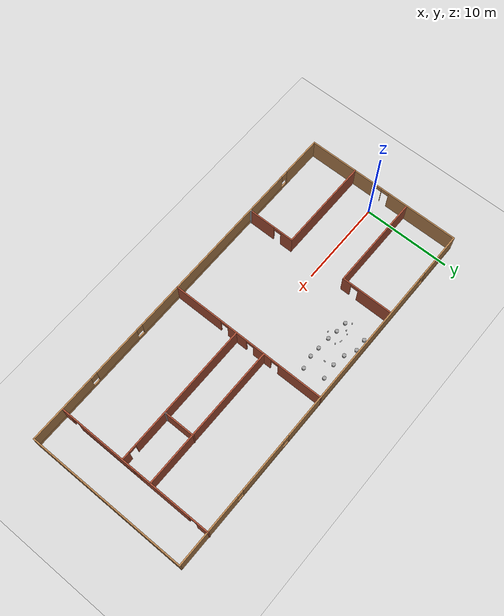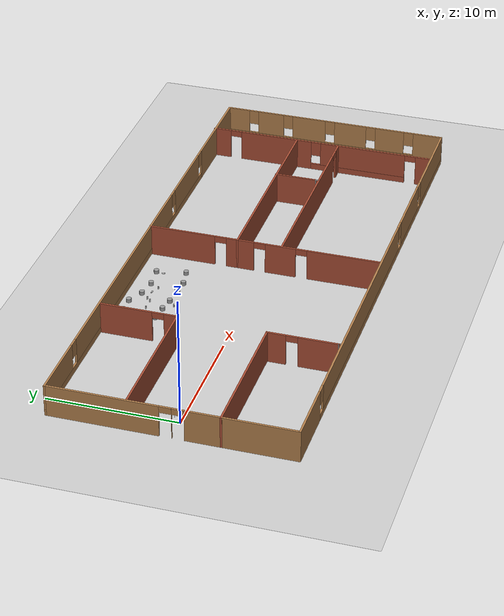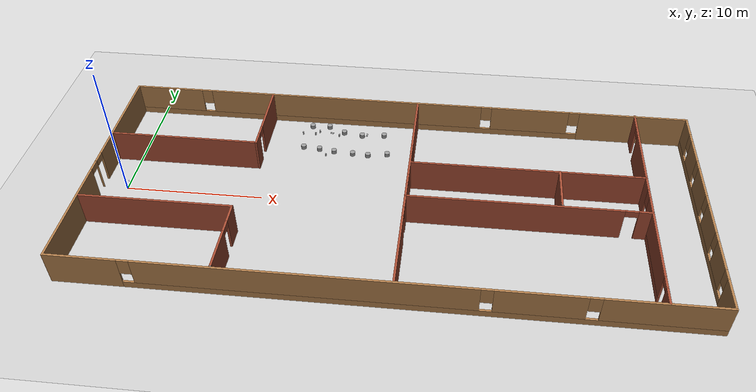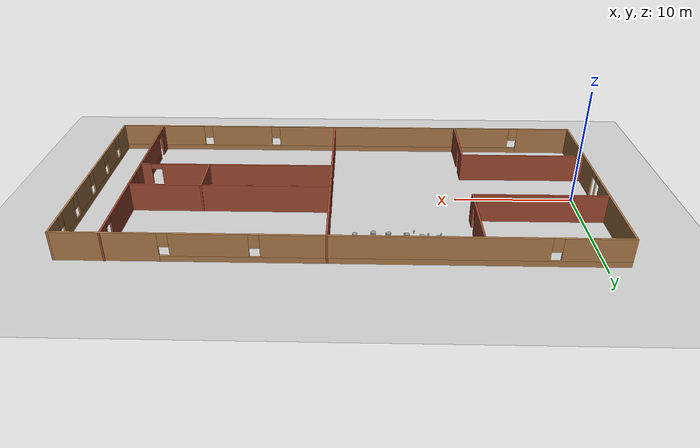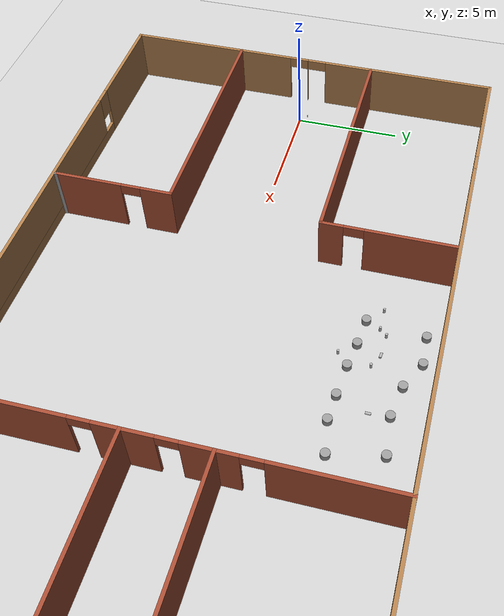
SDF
<sdf version="1.7">
 <world name="default">
  <light name="sun" type="directional">
   <pose>0 0 10 0 -0 0</pose>
   <diffuse>0.8 0.8 0.8 1</diffuse>
   <specular>0.2 0.2 0.2 1</specular>
   <attenuation>
    <range>1000</range>
    <constant>0.9</constant>
    <linear>0.01</linear>
    <quadratic>0.001</quadratic>
   </attenuation>
   <direction>-0.5 0.1 -0.9</direction>
   <spot><inner_angle>0</inner_angle><outer_angle>0</outer_angle><falloff>0</falloff></spot>
  </light>
  <model name="ground_plane">
   <static>1</static>
   <link name="link">
    <collision name="collision">
     <geometry><plane><normal>0 0 1</normal><size>100 100</size></plane></geometry>
     <surface>
      <contact><collide_bitmask>65535</collide_bitmask></contact>
      <friction><ode><mu>100</mu><mu2>50</mu2></ode></friction>
     </surface>
    </collision>
    <visual name="visual">
     <cast_shadows>0</cast_shadows>
     <geometry><plane><normal>0 0 1</normal><size>100 100</size></plane></geometry>
     <material>
      <script><uri>file://media/materials/scripts/gazebo.material</uri><name>Gazebo/Grey</name></script>
     </material>
    </visual>
   </link>
  </model>
  <gravity>0 0 -9.8</gravity>
  <magnetic_field>6e-06 2.3e-05 -4.2e-05</magnetic_field>
  <atmosphere type="adiabatic"/>
  <physics type="ode">
   <max_step_size>0.001</max_step_size>
   <real_time_factor>1</real_time_factor>
   <real_time_update_rate>1000</real_time_update_rate>
  </physics>
  <scene><ambient>0.4 0.4 0.4 1</ambient><background>0.7 0.7 0.7 1</background><shadows>1</shadows></scene>
  <spherical_coordinates>
   <surface_model>EARTH_WGS84</surface_model>
   <latitude_deg>0</latitude_deg>
   <longitude_deg>0</longitude_deg>
   <elevation>0</elevation>
   <heading_deg>0</heading_deg>
  </spherical_coordinates>
  <model name="godbomb_0">
   <link name="link_0">
    <inertial>
     <mass>0.5</mass>
     <inertia>
      <ixx>0.00042917</ixx>
      <ixy>0</ixy>
      <ixz>0</ixz>
      <iyy>0.00042917</iyy>
      <iyz>0</iyz>
      <izz>2.5e-05</izz>
     </inertia>
    </inertial>
    <visual name="ModelPreview_2::link_0::visual_2">
     <pose>0 0 -0.05 0 -0 0</pose>
     <geometry><cylinder><radius>0.02</radius><length>0.02</length></cylinder></geometry>
     <material>
      <lighting>1</lighting>
      <script><uri>file://media/materials/scripts/gazebo.material</uri><name>Gazebo/Grey</name></script>
      <shader type="pixel"><normal_map>__default__</normal_map></shader>
      <ambient>0.3 0.3 0.3 1</ambient>
      <diffuse>0.7 0.7 0.7 1</diffuse>
      <specular>0.01 0.01 0.01 1</specular>
      <emissive>0 0 0 1</emissive>
     </material>
    </visual>
    <visual name="visual">
     <geometry><cylinder><radius>0.01</radius><length>0.08</length></cylinder></geometry>
     <material>
      <lighting>1</lighting>
      <script><uri>file://media/materials/scripts/gazebo.material</uri><name>Gazebo/Grey</name></script>
      <shader type="pixel"><normal_map>__default__</normal_map></shader>
      <ambient>0.3 0.3 0.3 1</ambient>
      <diffuse>0.7 0.7 0.7 1</diffuse>
      <specular>0.01 0.01 0.01 1</specular>
      <emissive>0 0 0 1</emissive>
     </material>
    </visual>
    <visual name="ModelPreview_0::link_0::visual_1">
     <pose>0 0 0.05 0 -0 0</pose>
     <geometry><cylinder><radius>0.02</radius><length>0.02</length></cylinder></geometry>
     <material>
      <lighting>1</lighting>
      <script><uri>file://media/materials/scripts/gazebo.material</uri><name>Gazebo/Grey</name></script>
      <shader type="pixel"><normal_map>__default__</normal_map></shader>
      <ambient>0.3 0.3 0.3 1</ambient>
      <diffuse>0.7 0.7 0.7 1</diffuse>
      <specular>0.01 0.01 0.01 1</specular>
      <emissive>0 0 0 1</emissive>
     </material>
    </visual>
    <collision name="collision_2">
     <pose>0 0 -0.05 0 -0 0</pose>
     <geometry><cylinder><radius>0.02</radius><length>0.02</length></cylinder></geometry>
     <surface>
      <friction>
       <ode><mu>1</mu><mu2>1</mu2><fdir1>0 0 0</fdir1><slip1>0</slip1><slip2>0</slip2></ode>
       <torsional>
        <coefficient>1</coefficient>
        <patch_radius>0</patch_radius>
        <surface_radius>0</surface_radius>
        <use_patch_radius>1</use_patch_radius>
        <ode><slip>0</slip></ode>
       </torsional>
      </friction>
      <bounce><restitution_coefficient>0</restitution_coefficient><threshold>1e+06</threshold></bounce>
      <contact>
       <collide_without_contact>0</collide_without_contact>
       <collide_without_contact_bitmask>1</collide_without_contact_bitmask>
       <collide_bitmask>1</collide_bitmask>
       <ode>
        <soft_cfm>0</soft_cfm>
        <soft_erp>0.2</soft_erp>
        <kp>1e+13</kp>
        <kd>1</kd>
        <max_vel>0.01</max_vel>
        <min_depth>0</min_depth>
       </ode>
       <bullet>
        <split_impulse>1</split_impulse>
        <split_impulse_penetration_threshold>-0.01</split_impulse_penetration_threshold>
        <soft_cfm>0</soft_cfm>
        <soft_erp>0.2</soft_erp>
        <kp>1e+13</kp>
        <kd>1</kd>
       </bullet>
      </contact>
     </surface>
    </collision>
    <collision name="collision">
     <geometry><cylinder><radius>0.01</radius><length>0.08</length></cylinder></geometry>
     <surface>
      <friction>
       <ode><mu>1</mu><mu2>1</mu2><fdir1>0 0 0</fdir1><slip1>0</slip1><slip2>0</slip2></ode>
       <torsional>
        <coefficient>1</coefficient>
        <patch_radius>0</patch_radius>
        <surface_radius>0</surface_radius>
        <use_patch_radius>1</use_patch_radius>
        <ode><slip>0</slip></ode>
       </torsional>
      </friction>
      <bounce><restitution_coefficient>0</restitution_coefficient><threshold>1e+06</threshold></bounce>
      <contact>
       <collide_without_contact>0</collide_without_contact>
       <collide_without_contact_bitmask>1</collide_without_contact_bitmask>
       <collide_bitmask>1</collide_bitmask>
       <ode>
        <soft_cfm>0</soft_cfm>
        <soft_erp>0.2</soft_erp>
        <kp>1e+13</kp>
        <kd>1</kd>
        <max_vel>0.01</max_vel>
        <min_depth>0</min_depth>
       </ode>
       <bullet>
        <split_impulse>1</split_impulse>
        <split_impulse_penetration_threshold>-0.01</split_impulse_penetration_threshold>
        <soft_cfm>0</soft_cfm>
        <soft_erp>0.2</soft_erp>
        <kp>1e+13</kp>
        <kd>1</kd>
       </bullet>
      </contact>
     </surface>
    </collision>
    <collision name="collision_1">
     <pose>0 0 0.05 0 -0 0</pose>
     <geometry><cylinder><radius>0.02</radius><length>0.02</length></cylinder></geometry>
     <surface>
      <friction>
       <ode><mu>1</mu><mu2>1</mu2><fdir1>0 0 0</fdir1><slip1>0</slip1><slip2>0</slip2></ode>
       <torsional>
        <coefficient>1</coefficient>
        <patch_radius>0</patch_radius>
        <surface_radius>0</surface_radius>
        <use_patch_radius>1</use_patch_radius>
        <ode><slip>0</slip></ode>
       </torsional>
      </friction>
      <bounce><restitution_coefficient>0</restitution_coefficient><threshold>1e+06</threshold></bounce>
      <contact>
       <collide_without_contact>0</collide_without_contact>
       <collide_without_contact_bitmask>1</collide_without_contact_bitmask>
       <collide_bitmask>1</collide_bitmask>
       <ode>
        <soft_cfm>0</soft_cfm>
        <soft_erp>0.2</soft_erp>
        <kp>1e+13</kp>
        <kd>1</kd>
        <max_vel>0.01</max_vel>
        <min_depth>0</min_depth>
       </ode>
       <bullet>
        <split_impulse>1</split_impulse>
        <split_impulse_penetration_threshold>-0.01</split_impulse_penetration_threshold>
        <soft_cfm>0</soft_cfm>
        <soft_erp>0.2</soft_erp>
        <kp>1e+13</kp>
        <kd>1</kd>
       </bullet>
      </contact>
     </surface>
    </collision>
   </link>
   <static>0</static>
   <pose>0.026665 0.416817 0.377153 -1.5e-05 3e-06 8.8e-05</pose>
  </model>
  <model name="bighouse">
   <pose>19.6392 0.100979 0 0 -0 0</pose>
   <link name="Wall_16">
    <collision name="Wall_16_Collision">
     <geometry><box><size>11 0.15 2.5</size></box></geometry>
     <pose>0 0 1.25 0 -0 0</pose>
    </collision>
    <visual name="Wall_16_Visual">
     <pose>0 0 1.25 0 -0 0</pose>
     <geometry><box><size>11 0.15 2.5</size></box></geometry>
     <material>
      <script><uri>file://media/materials/scripts/gazebo.material</uri><name>Gazebo/Bricks</name></script>
      <ambient>1 1 1 1</ambient>
     </material>
     <meta><layer>0</layer></meta>
    </visual>
    <pose>-15.9308 3.16083 0 0 -0 0</pose>
   </link>
   <link name="Wall_19">
    <pose>-10.5058 6.08583 0 0 -0 1.5708</pose>
    <visual name="Wall_19_Visual_0">
     <pose>-2.46102 0 1.25 0 -0 0</pose>
     <geometry><box><size>1.07796 0.15 2.5</size></box></geometry>
     <material>
      <script><uri>file://media/materials/scripts/gazebo.material</uri><name>Gazebo/Bricks</name></script>
      <ambient>1 1 1 1</ambient>
     </material>
     <meta><layer>0</layer></meta>
    </visual>
    <collision name="Wall_19_Collision_0">
     <geometry><box><size>1.07796 0.15 2.5</size></box></geometry>
     <pose>-2.46102 0 1.25 0 -0 0</pose>
    </collision>
    <visual name="Wall_19_Visual_1">
     <pose>0.988979 0 1.25 0 -0 0</pose>
     <geometry><box><size>4.02204 0.15 2.5</size></box></geometry>
     <material>
      <script><uri>file://media/materials/scripts/gazebo.material</uri><name>Gazebo/Bricks</name></script>
      <ambient>1 1 1 1</ambient>
     </material>
     <meta><layer>0</layer></meta>
    </visual>
    <collision name="Wall_19_Collision_1">
     <geometry><box><size>4.02204 0.15 2.5</size></box></geometry>
     <pose>0.988979 0 1.25 0 -0 0</pose>
    </collision>
    <visual name="Wall_19_Visual_2">
     <pose>-1.47204 0 2.25 0 -0 0</pose>
     <geometry><box><size>0.9 0.15 0.5</size></box></geometry>
     <material>
      <script><uri>file://media/materials/scripts/gazebo.material</uri><name>Gazebo/Bricks</name></script>
      <ambient>1 1 1 1</ambient>
     </material>
     <meta><layer>0</layer></meta>
    </visual>
    <collision name="Wall_19_Collision_2">
     <geometry><box><size>0.9 0.15 0.5</size></box></geometry>
     <pose>-1.47204 0 2.25 0 -0 0</pose>
    </collision>
   </link>
   <link name="Wall_21">
    <collision name="Wall_21_Collision">
     <geometry><box><size>11 0.15 2.5</size></box></geometry>
     <pose>0 0 1.25 0 -0 0</pose>
    </collision>
    <visual name="Wall_21_Visual">
     <pose>0 0 1.25 0 -0 0</pose>
     <geometry><box><size>11 0.15 2.5</size></box></geometry>
     <material>
      <script><uri>file://media/materials/scripts/gazebo.material</uri><name>Gazebo/Bricks</name></script>
      <ambient>1 1 1 1</ambient>
     </material>
     <meta><layer>0</layer></meta>
    </visual>
    <pose>-16.0035 -3.64568 0 0 -0 0</pose>
   </link>
   <link name="Wall_22">
    <pose>-10.5785 -6.32069 0 0 -0 -1.5708</pose>
    <visual name="Wall_22_Visual_0">
     <pose>-2.0015 0 1.25 0 -0 0</pose>
     <geometry><box><size>1.49701 0.15 2.5</size></box></geometry>
     <material>
      <script><uri>file://media/materials/scripts/gazebo.material</uri><name>Gazebo/Bricks</name></script>
      <ambient>1 1 1 1</ambient>
     </material>
     <meta><layer>0</layer></meta>
    </visual>
    <collision name="Wall_22_Collision_0">
     <geometry><box><size>1.49701 0.15 2.5</size></box></geometry>
     <pose>-2.0015 0 1.25 0 -0 0</pose>
    </collision>
    <visual name="Wall_22_Visual_1">
     <pose>1.1985 0 1.25 0 -0 0</pose>
     <geometry><box><size>3.10299 0.15 2.5</size></box></geometry>
     <material>
      <script><uri>file://media/materials/scripts/gazebo.material</uri><name>Gazebo/Bricks</name></script>
      <ambient>1 1 1 1</ambient>
     </material>
     <meta><layer>0</layer></meta>
    </visual>
    <collision name="Wall_22_Collision_1">
     <geometry><box><size>3.10299 0.15 2.5</size></box></geometry>
     <pose>1.1985 0 1.25 0 -0 0</pose>
    </collision>
    <visual name="Wall_22_Visual_2">
     <pose>-0.802991 0 2.25 0 -0 0</pose>
     <geometry><box><size>0.9 0.15 0.5</size></box></geometry>
     <material>
      <script><uri>file://media/materials/scripts/gazebo.material</uri><name>Gazebo/Bricks</name></script>
      <ambient>1 1 1 1</ambient>
     </material>
     <meta><layer>0</layer></meta>
    </visual>
    <collision name="Wall_22_Collision_2">
     <geometry><box><size>0.9 0.15 0.5</size></box></geometry>
     <pose>-0.802991 0 2.25 0 -0 0</pose>
    </collision>
   </link>
   <link name="Wall_24">
    <collision name="Wall_24_Collision">
     <geometry><box><size>0.25 0.15 2.5</size></box></geometry>
     <pose>0 0 1.25 0 -0 0</pose>
    </collision>
    <visual name="Wall_24_Visual">
     <pose>0 0 1.25 0 -0 0</pose>
     <geometry><box><size>0.25 0.15 2.5</size></box></geometry>
     <material>
      <script><uri>file://media/materials/scripts/gazebo.material</uri><name>Gazebo/Grey</name></script>
      <ambient>1 1 1 1</ambient>
     </material>
     <meta><layer>0</layer></meta>
    </visual>
    <pose>-10.5655 -9.04398 0 0 -0 -1.309</pose>
   </link>
   <link name="Wall_28">
    <pose>0.951607 -0.015395 0 0 -0 -1.5708</pose>
    <visual name="Wall_28_Visual_0">
     <pose>-6.59547 0 1.25 0 -0 0</pose>
     <geometry><box><size>5.30905 0.15 2.5</size></box></geometry>
     <material>
      <script><uri>file://media/materials/scripts/gazebo.material</uri><name>Gazebo/Bricks</name></script>
      <ambient>1 1 1 1</ambient>
     </material>
     <meta><layer>0</layer></meta>
    </visual>
    <collision name="Wall_28_Collision_0">
     <geometry><box><size>5.30905 0.15 2.5</size></box></geometry>
     <pose>-6.59547 0 1.25 0 -0 0</pose>
    </collision>
    <visual name="Wall_28_Visual_1">
     <pose>-1.93341 0 1.25 0 -0 0</pose>
     <geometry><box><size>2.21508 0.15 2.5</size></box></geometry>
     <material>
      <script><uri>file://media/materials/scripts/gazebo.material</uri><name>Gazebo/Bricks</name></script>
      <ambient>1 1 1 1</ambient>
     </material>
     <meta><layer>0</layer></meta>
    </visual>
    <collision name="Wall_28_Collision_1">
     <geometry><box><size>2.21508 0.15 2.5</size></box></geometry>
     <pose>-1.93341 0 1.25 0 -0 0</pose>
    </collision>
    <visual name="Wall_28_Visual_2">
     <pose>1.28281 0 1.25 0 -0 0</pose>
     <geometry><box><size>2.41736 0.15 2.5</size></box></geometry>
     <material>
      <script><uri>file://media/materials/scripts/gazebo.material</uri><name>Gazebo/Bricks</name></script>
      <ambient>1 1 1 1</ambient>
     </material>
     <meta><layer>0</layer></meta>
    </visual>
    <collision name="Wall_28_Collision_2">
     <geometry><box><size>2.41736 0.15 2.5</size></box></geometry>
     <pose>1.28281 0 1.25 0 -0 0</pose>
    </collision>
    <visual name="Wall_28_Visual_3">
     <pose>6.32075 0 1.25 0 -0 0</pose>
     <geometry><box><size>5.85851 0.15 2.5</size></box></geometry>
     <material>
      <script><uri>file://media/materials/scripts/gazebo.material</uri><name>Gazebo/Bricks</name></script>
      <ambient>1 1 1 1</ambient>
     </material>
     <meta><layer>0</layer></meta>
    </visual>
    <collision name="Wall_28_Collision_3">
     <geometry><box><size>5.85851 0.15 2.5</size></box></geometry>
     <pose>6.32075 0 1.25 0 -0 0</pose>
    </collision>
    <visual name="Wall_28_Visual_4">
     <pose>-3.49095 0 2.25 0 -0 0</pose>
     <geometry><box><size>0.9 0.15 0.5</size></box></geometry>
     <material>
      <script><uri>file://media/materials/scripts/gazebo.material</uri><name>Gazebo/Bricks</name></script>
      <ambient>1 1 1 1</ambient>
     </material>
     <meta><layer>0</layer></meta>
    </visual>
    <collision name="Wall_28_Collision_4">
     <geometry><box><size>0.9 0.15 0.5</size></box></geometry>
     <pose>-3.49095 0 2.25 0 -0 0</pose>
    </collision>
    <visual name="Wall_28_Visual_5">
     <pose>-0.375866 0 2.25 0 -0 0</pose>
     <geometry><box><size>0.9 0.15 0.5</size></box></geometry>
     <material>
      <script><uri>file://media/materials/scripts/gazebo.material</uri><name>Gazebo/Bricks</name></script>
      <ambient>1 1 1 1</ambient>
     </material>
     <meta><layer>0</layer></meta>
    </visual>
    <collision name="Wall_28_Collision_5">
     <geometry><box><size>0.9 0.15 0.5</size></box></geometry>
     <pose>-0.375866 0 2.25 0 -0 0</pose>
    </collision>
    <visual name="Wall_28_Visual_6">
     <pose>2.94149 0 2.25 0 -0 0</pose>
     <geometry><box><size>0.9 0.15 0.5</size></box></geometry>
     <material>
      <script><uri>file://media/materials/scripts/gazebo.material</uri><name>Gazebo/Bricks</name></script>
      <ambient>1 1 1 1</ambient>
     </material>
     <meta><layer>0</layer></meta>
    </visual>
    <collision name="Wall_28_Collision_6">
     <geometry><box><size>0.9 0.15 0.5</size></box></geometry>
     <pose>2.94149 0 2.25 0 -0 0</pose>
    </collision>
   </link>
   <link name="Wall_30">
    <pose>17.5788 0.025061 0 0 -0 -1.5708</pose>
    <visual name="Wall_30_Visual_0">
     <pose>-8.51711 0 1.25 0 -0 0</pose>
     <geometry><box><size>1.46578 0.15 2.5</size></box></geometry>
     <material>
      <script><uri>file://media/materials/scripts/gazebo.material</uri><name>Gazebo/Bricks</name></script>
      <ambient>1 1 1 1</ambient>
     </material>
     <meta><layer>0</layer></meta>
    </visual>
    <collision name="Wall_30_Collision_0">
     <geometry><box><size>1.46578 0.15 2.5</size></box></geometry>
     <pose>-8.51711 0 1.25 0 -0 0</pose>
    </collision>
    <visual name="Wall_30_Visual_1">
     <pose>-3.8705 0 1.25 0 -0 0</pose>
     <geometry><box><size>6.02745 0.15 2.5</size></box></geometry>
     <material>
      <script><uri>file://media/materials/scripts/gazebo.material</uri><name>Gazebo/Bricks</name></script>
      <ambient>1 1 1 1</ambient>
     </material>
     <meta><layer>0</layer></meta>
    </visual>
    <collision name="Wall_30_Collision_1">
     <geometry><box><size>6.02745 0.15 2.5</size></box></geometry>
     <pose>-3.8705 0 1.25 0 -0 0</pose>
    </collision>
    <visual name="Wall_30_Visual_2">
     <pose>8.60649 0 1.25 0 -0 0</pose>
     <geometry><box><size>1.28703 0.15 2.5</size></box></geometry>
     <material>
      <script><uri>file://media/materials/scripts/gazebo.material</uri><name>Gazebo/Bricks</name></script>
      <ambient>1 1 1 1</ambient>
     </material>
     <meta><layer>0</layer></meta>
    </visual>
    <collision name="Wall_30_Collision_2">
     <geometry><box><size>1.28703 0.15 2.5</size></box></geometry>
     <pose>8.60649 0 1.25 0 -0 0</pose>
    </collision>
    <visual name="Wall_30_Visual_3">
     <pose>3.1031 0 0.25 0 -0 0</pose>
     <geometry><box><size>7.91975 0.15 0.5</size></box></geometry>
     <material>
      <script><uri>file://media/materials/scripts/gazebo.material</uri><name>Gazebo/Bricks</name></script>
      <ambient>1 1 1 1</ambient>
     </material>
     <meta><layer>0</layer></meta>
    </visual>
    <collision name="Wall_30_Collision_3">
     <geometry><box><size>7.91975 0.15 0.5</size></box></geometry>
     <pose>3.1031 0 0.25 0 -0 0</pose>
    </collision>
    <visual name="Wall_30_Visual_4">
     <pose>3.5031 0 1.5 0 -0 0</pose>
     <geometry><box><size>7.11975 0.15 2</size></box></geometry>
     <material>
      <script><uri>file://media/materials/scripts/gazebo.material</uri><name>Gazebo/Bricks</name></script>
      <ambient>1 1 1 1</ambient>
     </material>
     <meta><layer>0</layer></meta>
    </visual>
    <collision name="Wall_30_Collision_4">
     <geometry><box><size>7.11975 0.15 2</size></box></geometry>
     <pose>3.5031 0 1.5 0 -0 0</pose>
    </collision>
    <visual name="Wall_30_Visual_5">
     <pose>-0.456777 0 1.9 0 -0 0</pose>
     <geometry><box><size>0.8 0.15 1.2</size></box></geometry>
     <material>
      <script><uri>file://media/materials/scripts/gazebo.material</uri><name>Gazebo/Bricks</name></script>
      <ambient>1 1 1 1</ambient>
     </material>
     <meta><layer>0</layer></meta>
    </visual>
    <collision name="Wall_30_Collision_5">
     <geometry><box><size>0.8 0.15 1.2</size></box></geometry>
     <pose>-0.456777 0 1.9 0 -0 0</pose>
    </collision>
    <visual name="Wall_30_Visual_6">
     <pose>-7.33422 0 2.25 0 -0 0</pose>
     <geometry><box><size>0.9 0.15 0.5</size></box></geometry>
     <material>
      <script><uri>file://media/materials/scripts/gazebo.material</uri><name>Gazebo/Bricks</name></script>
      <ambient>1 1 1 1</ambient>
     </material>
     <meta><layer>0</layer></meta>
    </visual>
    <collision name="Wall_30_Collision_6">
     <geometry><box><size>0.9 0.15 0.5</size></box></geometry>
     <pose>-7.33422 0 2.25 0 -0 0</pose>
    </collision>
    <visual name="Wall_30_Visual_7">
     <pose>7.51297 0 2.25 0 -0 0</pose>
     <geometry><box><size>0.9 0.15 0.5</size></box></geometry>
     <material>
      <script><uri>file://media/materials/scripts/gazebo.material</uri><name>Gazebo/Bricks</name></script>
      <ambient>1 1 1 1</ambient>
     </material>
     <meta><layer>0</layer></meta>
    </visual>
    <collision name="Wall_30_Collision_7">
     <geometry><box><size>0.9 0.15 0.5</size></box></geometry>
     <pose>7.51297 0 2.25 0 -0 0</pose>
    </collision>
   </link>
   <link name="Wall_34">
    <collision name="Wall_34_Collision">
     <geometry><box><size>16.75 0.15 2.5</size></box></geometry>
     <pose>0 0 1.25 0 -0 0</pose>
    </collision>
    <visual name="Wall_34_Visual">
     <pose>0 0 1.25 0 -0 0</pose>
     <geometry><box><size>16.75 0.15 2.5</size></box></geometry>
     <material>
      <script><uri>file://media/materials/scripts/gazebo.material</uri><name>Gazebo/Bricks</name></script>
      <ambient>1 1 1 1</ambient>
     </material>
     <meta><layer>0</layer></meta>
    </visual>
    <pose>9.25161 2.12033 0 0 -0 0</pose>
   </link>
   <link name="Wall_36">
    <pose>9.25161 -1.3993 0 0 -0 0</pose>
    <visual name="Wall_36_Visual_0">
     <pose>-0.938142 0 1.25 0 -0 0</pose>
     <geometry><box><size>14.8737 0.15 2.5</size></box></geometry>
     <material>
      <script><uri>file://media/materials/scripts/gazebo.material</uri><name>Gazebo/Bricks</name></script>
      <ambient>1 1 1 1</ambient>
     </material>
     <meta><layer>0</layer></meta>
    </visual>
    <collision name="Wall_36_Collision_0">
     <geometry><box><size>14.8737 0.15 2.5</size></box></geometry>
     <pose>-0.938142 0 1.25 0 -0 0</pose>
    </collision>
    <visual name="Wall_36_Visual_1">
     <pose>7.88686 0 1.25 0 -0 0</pose>
     <geometry><box><size>0.976284 0.15 2.5</size></box></geometry>
     <material>
      <script><uri>file://media/materials/scripts/gazebo.material</uri><name>Gazebo/Bricks</name></script>
      <ambient>1 1 1 1</ambient>
     </material>
     <meta><layer>0</layer></meta>
    </visual>
    <collision name="Wall_36_Collision_1">
     <geometry><box><size>0.976284 0.15 2.5</size></box></geometry>
     <pose>7.88686 0 1.25 0 -0 0</pose>
    </collision>
    <visual name="Wall_36_Visual_2">
     <pose>6.94872 0 2.25 0 -0 0</pose>
     <geometry><box><size>0.9 0.15 0.5</size></box></geometry>
     <material>
      <script><uri>file://media/materials/scripts/gazebo.material</uri><name>Gazebo/Bricks</name></script>
      <ambient>1 1 1 1</ambient>
     </material>
     <meta><layer>0</layer></meta>
    </visual>
    <collision name="Wall_36_Collision_2">
     <geometry><box><size>0.9 0.15 0.5</size></box></geometry>
     <pose>6.94872 0 2.25 0 -0 0</pose>
    </collision>
   </link>
   <link name="Wall_40">
    <collision name="Wall_40_Collision">
     <geometry><box><size>3.5 0.15 2.5</size></box></geometry>
     <pose>0 0 1.25 0 -0 0</pose>
    </collision>
    <visual name="Wall_40_Visual">
     <pose>0 0 1.25 0 -0 0</pose>
     <geometry><box><size>3.5 0.15 2.5</size></box></geometry>
     <material>
      <script><uri>file://media/materials/scripts/gazebo.material</uri><name>Gazebo/Bricks</name></script>
      <ambient>1 1 1 1</ambient>
     </material>
     <meta><layer>0</layer></meta>
    </visual>
    <pose>11.5914 0.48579 0 0 -0 -1.5708</pose>
   </link>
   <link name="Wall_41">
    <collision name="Wall_41_Collision">
     <geometry><box><size>0.25 0.15 2.5</size></box></geometry>
     <pose>0 0 1.25 0 -0 0</pose>
    </collision>
    <visual name="Wall_41_Visual">
     <pose>0 0 1.25 0 -0 0</pose>
     <geometry><box><size>0.25 0.15 2.5</size></box></geometry>
     <material>
      <script><uri>file://media/materials/scripts/gazebo.material</uri><name>Gazebo/Grey</name></script>
      <ambient>1 1 1 1</ambient>
     </material>
     <meta><layer>0</layer></meta>
    </visual>
    <pose>11.6044 -1.23751 0 0 -0 -1.309</pose>
   </link>
   <link name="Wall_6">
    <pose>-21.4215 -0.025061 0 0 -0 -1.5708</pose>
    <visual name="Wall_6_Visual_0">
     <pose>-5.04277 0 1.25 0 -0 0</pose>
     <geometry><box><size>8.41447 0.15 2.5</size></box></geometry>
     <material>
      <script><uri>file://media/materials/scripts/gazebo.material</uri><name>Gazebo/Wood</name></script>
      <ambient>1 1 1 1</ambient>
     </material>
     <meta><layer>0</layer></meta>
    </visual>
    <collision name="Wall_6_Collision_0">
     <geometry><box><size>8.41447 0.15 2.5</size></box></geometry>
     <pose>-5.04277 0 1.25 0 -0 0</pose>
    </collision>
    <visual name="Wall_6_Visual_1">
     <pose>0.073447 0 1.25 0 -0 0</pose>
     <geometry><box><size>0.017959 0.15 2.5</size></box></geometry>
     <material>
      <script><uri>file://media/materials/scripts/gazebo.material</uri><name>Gazebo/Wood</name></script>
      <ambient>1 1 1 1</ambient>
     </material>
     <meta><layer>0</layer></meta>
    </visual>
    <collision name="Wall_6_Collision_1">
     <geometry><box><size>0.017959 0.15 2.5</size></box></geometry>
     <pose>0.073447 0 1.25 0 -0 0</pose>
    </collision>
    <visual name="Wall_6_Visual_2">
     <pose>5.11621 0 1.25 0 -0 0</pose>
     <geometry><box><size>8.26757 0.15 2.5</size></box></geometry>
     <material>
      <script><uri>file://media/materials/scripts/gazebo.material</uri><name>Gazebo/Wood</name></script>
      <ambient>1 1 1 1</ambient>
     </material>
     <meta><layer>0</layer></meta>
    </visual>
    <collision name="Wall_6_Collision_2">
     <geometry><box><size>8.26757 0.15 2.5</size></box></geometry>
     <pose>5.11621 0 1.25 0 -0 0</pose>
    </collision>
    <visual name="Wall_6_Visual_3">
     <pose>-0.385532 0 2.25 0 -0 0</pose>
     <geometry><box><size>0.9 0.15 0.5</size></box></geometry>
     <material>
      <script><uri>file://media/materials/scripts/gazebo.material</uri><name>Gazebo/Wood</name></script>
      <ambient>1 1 1 1</ambient>
     </material>
     <meta><layer>0</layer></meta>
    </visual>
    <collision name="Wall_6_Collision_3">
     <geometry><box><size>0.9 0.15 0.5</size></box></geometry>
     <pose>-0.385532 0 2.25 0 -0 0</pose>
    </collision>
    <visual name="Wall_6_Visual_4">
     <pose>0.532427 0 2.25 0 -0 0</pose>
     <geometry><box><size>0.9 0.15 0.5</size></box></geometry>
     <material>
      <script><uri>file://media/materials/scripts/gazebo.material</uri><name>Gazebo/Wood</name></script>
      <ambient>1 1 1 1</ambient>
     </material>
     <meta><layer>0</layer></meta>
    </visual>
    <collision name="Wall_6_Collision_4">
     <geometry><box><size>0.9 0.15 0.5</size></box></geometry>
     <pose>0.532427 0 2.25 0 -0 0</pose>
    </collision>
   </link>
   <link name="Wall_7">
    <pose>0.003474 -9.20006 0 0 -0 0</pose>
    <visual name="Wall_7_Visual_0">
     <pose>-19.054 0 1.25 0 -0 0</pose>
     <geometry><box><size>4.89193 0.15 2.5</size></box></geometry>
     <material>
      <script><uri>file://media/materials/scripts/gazebo.material</uri><name>Gazebo/Wood</name></script>
      <ambient>1 1 1 1</ambient>
     </material>
     <meta><layer>0</layer></meta>
    </visual>
    <collision name="Wall_7_Collision_0">
     <geometry><box><size>4.89193 0.15 2.5</size></box></geometry>
     <pose>-19.054 0 1.25 0 -0 0</pose>
    </collision>
    <visual name="Wall_7_Visual_1">
     <pose>2.44597 0 0.25 0 -0 0</pose>
     <geometry><box><size>38.1081 0.15 0.5</size></box></geometry>
     <material>
      <script><uri>file://media/materials/scripts/gazebo.material</uri><name>Gazebo/Wood</name></script>
      <ambient>1 1 1 1</ambient>
     </material>
     <meta><layer>0</layer></meta>
    </visual>
    <collision name="Wall_7_Collision_1">
     <geometry><box><size>38.1081 0.15 0.5</size></box></geometry>
     <pose>2.44597 0 0.25 0 -0 0</pose>
    </collision>
    <visual name="Wall_7_Visual_2">
     <pose>-4.75914 0 1.5 0 -0 0</pose>
     <geometry><box><size>22.0979 0.15 2</size></box></geometry>
     <material>
      <script><uri>file://media/materials/scripts/gazebo.material</uri><name>Gazebo/Wood</name></script>
      <ambient>1 1 1 1</ambient>
     </material>
     <meta><layer>0</layer></meta>
    </visual>
    <collision name="Wall_7_Collision_2">
     <geometry><box><size>22.0979 0.15 2</size></box></geometry>
     <pose>-4.75914 0 1.5 0 -0 0</pose>
    </collision>
    <visual name="Wall_7_Visual_3">
     <pose>9.96669 0 1.5 0 -0 0</pose>
     <geometry><box><size>5.7538 0.15 2</size></box></geometry>
     <material>
      <script><uri>file://media/materials/scripts/gazebo.material</uri><name>Gazebo/Wood</name></script>
      <ambient>1 1 1 1</ambient>
     </material>
     <meta><layer>0</layer></meta>
    </visual>
    <collision name="Wall_7_Collision_3">
     <geometry><box><size>5.7538 0.15 2</size></box></geometry>
     <pose>9.96669 0 1.5 0 -0 0</pose>
    </collision>
    <visual name="Wall_7_Visual_4">
     <pose>17.5718 0 1.5 0 -0 0</pose>
     <geometry><box><size>7.85641 0.15 2</size></box></geometry>
     <material>
      <script><uri>file://media/materials/scripts/gazebo.material</uri><name>Gazebo/Wood</name></script>
      <ambient>1 1 1 1</ambient>
     </material>
     <meta><layer>0</layer></meta>
    </visual>
    <collision name="Wall_7_Collision_4">
     <geometry><box><size>7.85641 0.15 2</size></box></geometry>
     <pose>17.5718 0 1.5 0 -0 0</pose>
    </collision>
    <visual name="Wall_7_Visual_5">
     <pose>-16.2081 0 1.9 0 -0 0</pose>
     <geometry><box><size>0.8 0.15 1.2</size></box></geometry>
     <material>
      <script><uri>file://media/materials/scripts/gazebo.material</uri><name>Gazebo/Wood</name></script>
      <ambient>1 1 1 1</ambient>
     </material>
     <meta><layer>0</layer></meta>
    </visual>
    <collision name="Wall_7_Collision_5">
     <geometry><box><size>0.8 0.15 1.2</size></box></geometry>
     <pose>-16.2081 0 1.9 0 -0 0</pose>
    </collision>
    <visual name="Wall_7_Visual_6">
     <pose>6.68979 0 1.9 0 -0 0</pose>
     <geometry><box><size>0.8 0.15 1.2</size></box></geometry>
     <material>
      <script><uri>file://media/materials/scripts/gazebo.material</uri><name>Gazebo/Wood</name></script>
      <ambient>1 1 1 1</ambient>
     </material>
     <meta><layer>0</layer></meta>
    </visual>
    <collision name="Wall_7_Collision_6">
     <geometry><box><size>0.8 0.15 1.2</size></box></geometry>
     <pose>6.68979 0 1.9 0 -0 0</pose>
    </collision>
    <visual name="Wall_7_Visual_7">
     <pose>13.2436 0 1.9 0 -0 0</pose>
     <geometry><box><size>0.8 0.15 1.2</size></box></geometry>
     <material>
      <script><uri>file://media/materials/scripts/gazebo.material</uri><name>Gazebo/Wood</name></script>
      <ambient>1 1 1 1</ambient>
     </material>
     <meta><layer>0</layer></meta>
    </visual>
    <collision name="Wall_7_Collision_7">
     <geometry><box><size>0.8 0.15 1.2</size></box></geometry>
     <pose>13.2436 0 1.9 0 -0 0</pose>
    </collision>
   </link>
   <link name="Wall_8">
    <pose>21.4285 -0.025061 0 0 -0 1.5708</pose>
    <visual name="Wall_8_Visual_0">
     <pose>-8.0305 0 1.25 0 -0 0</pose>
     <geometry><box><size>2.43899 0.15 2.5</size></box></geometry>
     <material>
      <script><uri>file://media/materials/scripts/gazebo.material</uri><name>Gazebo/Wood</name></script>
      <ambient>1 1 1 1</ambient>
     </material>
     <meta><layer>0</layer></meta>
    </visual>
    <collision name="Wall_8_Collision_0">
     <geometry><box><size>2.43899 0.15 2.5</size></box></geometry>
     <pose>-8.0305 0 1.25 0 -0 0</pose>
    </collision>
    <visual name="Wall_8_Visual_1">
     <pose>1.2195 0 0.25 0 -0 0</pose>
     <geometry><box><size>16.061 0.15 0.5</size></box></geometry>
     <material>
      <script><uri>file://media/materials/scripts/gazebo.material</uri><name>Gazebo/Wood</name></script>
      <ambient>1 1 1 1</ambient>
     </material>
     <meta><layer>0</layer></meta>
    </visual>
    <collision name="Wall_8_Collision_1">
     <geometry><box><size>16.061 0.15 0.5</size></box></geometry>
     <pose>1.2195 0 0.25 0 -0 0</pose>
    </collision>
    <visual name="Wall_8_Visual_2">
     <pose>-4.79278 0 1.5 0 -0 0</pose>
     <geometry><box><size>2.43645 0.15 2</size></box></geometry>
     <material>
      <script><uri>file://media/materials/scripts/gazebo.material</uri><name>Gazebo/Wood</name></script>
      <ambient>1 1 1 1</ambient>
     </material>
     <meta><layer>0</layer></meta>
    </visual>
    <collision name="Wall_8_Collision_2">
     <geometry><box><size>2.43645 0.15 2</size></box></geometry>
     <pose>-4.79278 0 1.5 0 -0 0</pose>
    </collision>
    <visual name="Wall_8_Visual_3">
     <pose>-1.41474 0 1.5 0 -0 0</pose>
     <geometry><box><size>2.71963 0.15 2</size></box></geometry>
     <material>
      <script><uri>file://media/materials/scripts/gazebo.material</uri><name>Gazebo/Wood</name></script>
      <ambient>1 1 1 1</ambient>
     </material>
     <meta><layer>0</layer></meta>
    </visual>
    <collision name="Wall_8_Collision_3">
     <geometry><box><size>2.71963 0.15 2</size></box></geometry>
     <pose>-1.41474 0 1.5 0 -0 0</pose>
    </collision>
    <visual name="Wall_8_Visual_4">
     <pose>2.16558 0 1.5 0 -0 0</pose>
     <geometry><box><size>2.841 0.15 2</size></box></geometry>
     <material>
      <script><uri>file://media/materials/scripts/gazebo.material</uri><name>Gazebo/Wood</name></script>
      <ambient>1 1 1 1</ambient>
     </material>
     <meta><layer>0</layer></meta>
    </visual>
    <collision name="Wall_8_Collision_4">
     <geometry><box><size>2.841 0.15 2</size></box></geometry>
     <pose>2.16558 0 1.5 0 -0 0</pose>
    </collision>
    <visual name="Wall_8_Visual_5">
     <pose>5.48294 0 1.5 0 -0 0</pose>
     <geometry><box><size>2.19371 0.15 2</size></box></geometry>
     <material>
      <script><uri>file://media/materials/scripts/gazebo.material</uri><name>Gazebo/Wood</name></script>
      <ambient>1 1 1 1</ambient>
     </material>
     <meta><layer>0</layer></meta>
    </visual>
    <collision name="Wall_8_Collision_5">
     <geometry><box><size>2.19371 0.15 2</size></box></geometry>
     <pose>5.48294 0 1.5 0 -0 0</pose>
    </collision>
    <visual name="Wall_8_Visual_6">
     <pose>8.3149 0 1.5 0 -0 0</pose>
     <geometry><box><size>1.87021 0.15 2</size></box></geometry>
     <material>
      <script><uri>file://media/materials/scripts/gazebo.material</uri><name>Gazebo/Wood</name></script>
      <ambient>1 1 1 1</ambient>
     </material>
     <meta><layer>0</layer></meta>
    </visual>
    <collision name="Wall_8_Collision_6">
     <geometry><box><size>1.87021 0.15 2</size></box></geometry>
     <pose>8.3149 0 1.5 0 -0 0</pose>
    </collision>
    <visual name="Wall_8_Visual_7">
     <pose>-6.41101 0 1.9 0 -0 0</pose>
     <geometry><box><size>0.8 0.15 1.2</size></box></geometry>
     <material>
      <script><uri>file://media/materials/scripts/gazebo.material</uri><name>Gazebo/Wood</name></script>
      <ambient>1 1 1 1</ambient>
     </material>
     <meta><layer>0</layer></meta>
    </visual>
    <collision name="Wall_8_Collision_7">
     <geometry><box><size>0.8 0.15 1.2</size></box></geometry>
     <pose>-6.41101 0 1.9 0 -0 0</pose>
    </collision>
    <visual name="Wall_8_Visual_8">
     <pose>-3.17456 0 1.9 0 -0 0</pose>
     <geometry><box><size>0.8 0.15 1.2</size></box></geometry>
     <material>
      <script><uri>file://media/materials/scripts/gazebo.material</uri><name>Gazebo/Wood</name></script>
      <ambient>1 1 1 1</ambient>
     </material>
     <meta><layer>0</layer></meta>
    </visual>
    <collision name="Wall_8_Collision_8">
     <geometry><box><size>0.8 0.15 1.2</size></box></geometry>
     <pose>-3.17456 0 1.9 0 -0 0</pose>
    </collision>
    <visual name="Wall_8_Visual_9">
     <pose>0.345077 0 1.9 0 -0 0</pose>
     <geometry><box><size>0.8 0.15 1.2</size></box></geometry>
     <material>
      <script><uri>file://media/materials/scripts/gazebo.material</uri><name>Gazebo/Wood</name></script>
      <ambient>1 1 1 1</ambient>
     </material>
     <meta><layer>0</layer></meta>
    </visual>
    <collision name="Wall_8_Collision_9">
     <geometry><box><size>0.8 0.15 1.2</size></box></geometry>
     <pose>0.345077 0 1.9 0 -0 0</pose>
    </collision>
    <visual name="Wall_8_Visual_10">
     <pose>3.98608 0 1.9 0 -0 0</pose>
     <geometry><box><size>0.8 0.15 1.2</size></box></geometry>
     <material>
      <script><uri>file://media/materials/scripts/gazebo.material</uri><name>Gazebo/Wood</name></script>
      <ambient>1 1 1 1</ambient>
     </material>
     <meta><layer>0</layer></meta>
    </visual>
    <collision name="Wall_8_Collision_10">
     <geometry><box><size>0.8 0.15 1.2</size></box></geometry>
     <pose>3.98608 0 1.9 0 -0 0</pose>
    </collision>
    <visual name="Wall_8_Visual_11">
     <pose>6.97979 0 1.9 0 -0 0</pose>
     <geometry><box><size>0.8 0.15 1.2</size></box></geometry>
     <material>
      <script><uri>file://media/materials/scripts/gazebo.material</uri><name>Gazebo/Wood</name></script>
      <ambient>1 1 1 1</ambient>
     </material>
     <meta><layer>0</layer></meta>
    </visual>
    <collision name="Wall_8_Collision_11">
     <geometry><box><size>0.8 0.15 1.2</size></box></geometry>
     <pose>6.97979 0 1.9 0 -0 0</pose>
    </collision>
   </link>
   <link name="Wall_9">
    <pose>0.003474 9.14994 0 0 -0 3.14159</pose>
    <visual name="Wall_9_Visual_0">
     <pose>-17.4504 0 1.25 0 -0 0</pose>
     <geometry><box><size>8.09914 0.15 2.5</size></box></geometry>
     <material>
      <script><uri>file://media/materials/scripts/gazebo.material</uri><name>Gazebo/Wood</name></script>
      <ambient>1 1 1 1</ambient>
     </material>
     <meta><layer>0</layer></meta>
    </visual>
    <collision name="Wall_9_Collision_0">
     <geometry><box><size>8.09914 0.15 2.5</size></box></geometry>
     <pose>-17.4504 0 1.25 0 -0 0</pose>
    </collision>
    <visual name="Wall_9_Visual_1">
     <pose>4.04957 0 0.25 0 -0 0</pose>
     <geometry><box><size>34.9009 0.15 0.5</size></box></geometry>
     <material>
      <script><uri>file://media/materials/scripts/gazebo.material</uri><name>Gazebo/Wood</name></script>
      <ambient>1 1 1 1</ambient>
     </material>
     <meta><layer>0</layer></meta>
    </visual>
    <collision name="Wall_9_Collision_1">
     <geometry><box><size>34.9009 0.15 0.5</size></box></geometry>
     <pose>4.04957 0 0.25 0 -0 0</pose>
    </collision>
    <visual name="Wall_9_Visual_2">
     <pose>-9.64305 0 1.5 0 -0 0</pose>
     <geometry><box><size>5.91563 0.15 2</size></box></geometry>
     <material>
      <script><uri>file://media/materials/scripts/gazebo.material</uri><name>Gazebo/Wood</name></script>
      <ambient>1 1 1 1</ambient>
     </material>
     <meta><layer>0</layer></meta>
    </visual>
    <collision name="Wall_9_Collision_2">
     <geometry><box><size>5.91563 0.15 2</size></box></geometry>
     <pose>-9.64305 0 1.5 0 -0 0</pose>
    </collision>
    <visual name="Wall_9_Visual_3">
     <pose>4.77937 0 1.5 0 -0 0</pose>
     <geometry><box><size>21.3292 0.15 2</size></box></geometry>
     <material>
      <script><uri>file://media/materials/scripts/gazebo.material</uri><name>Gazebo/Wood</name></script>
      <ambient>1 1 1 1</ambient>
     </material>
     <meta><layer>0</layer></meta>
    </visual>
    <collision name="Wall_9_Collision_3">
     <geometry><box><size>21.3292 0.15 2</size></box></geometry>
     <pose>4.77937 0 1.5 0 -0 0</pose>
    </collision>
    <visual name="Wall_9_Visual_4">
     <pose>18.872 0 1.5 0 -0 0</pose>
     <geometry><box><size>5.25603 0.15 2</size></box></geometry>
     <material>
      <script><uri>file://media/materials/scripts/gazebo.material</uri><name>Gazebo/Wood</name></script>
      <ambient>1 1 1 1</ambient>
     </material>
     <meta><layer>0</layer></meta>
    </visual>
    <collision name="Wall_9_Collision_4">
     <geometry><box><size>5.25603 0.15 2</size></box></geometry>
     <pose>18.872 0 1.5 0 -0 0</pose>
    </collision>
    <visual name="Wall_9_Visual_5">
     <pose>-13.0009 0 1.9 0 -0 0</pose>
     <geometry><box><size>0.8 0.15 1.2</size></box></geometry>
     <material>
      <script><uri>file://media/materials/scripts/gazebo.material</uri><name>Gazebo/Wood</name></script>
      <ambient>1 1 1 1</ambient>
     </material>
     <meta><layer>0</layer></meta>
    </visual>
    <collision name="Wall_9_Collision_5">
     <geometry><box><size>0.8 0.15 1.2</size></box></geometry>
     <pose>-13.0009 0 1.9 0 -0 0</pose>
    </collision>
    <visual name="Wall_9_Visual_6">
     <pose>-6.28523 0 1.9 0 -0 0</pose>
     <geometry><box><size>0.8 0.15 1.2</size></box></geometry>
     <material>
      <script><uri>file://media/materials/scripts/gazebo.material</uri><name>Gazebo/Wood</name></script>
      <ambient>1 1 1 1</ambient>
     </material>
     <meta><layer>0</layer></meta>
    </visual>
    <collision name="Wall_9_Collision_6">
     <geometry><box><size>0.8 0.15 1.2</size></box></geometry>
     <pose>-6.28523 0 1.9 0 -0 0</pose>
    </collision>
    <visual name="Wall_9_Visual_7">
     <pose>15.844 0 1.9 0 -0 0</pose>
     <geometry><box><size>0.8 0.15 1.2</size></box></geometry>
     <material>
      <script><uri>file://media/materials/scripts/gazebo.material</uri><name>Gazebo/Wood</name></script>
      <ambient>1 1 1 1</ambient>
     </material>
     <meta><layer>0</layer></meta>
    </visual>
    <collision name="Wall_9_Collision_7">
     <geometry><box><size>0.8 0.15 1.2</size></box></geometry>
     <pose>15.844 0 1.9 0 -0 0</pose>
    </collision>
   </link>
   <static>1</static>
  </model>
  <model name="beer">
   <link name="link">
    <pose>0 0 0.115 0 -0 0</pose>
    <inertial>
     <mass>0.39</mass>
     <inertia><ixx>0.00058</ixx><ixy>0</ixy><ixz>0</ixz><iyy>0.00058</iyy><iyz>0</iyz><izz>0.00019</izz></inertia>
    </inertial>
    <collision name="collision">
     <geometry><cylinder><radius>0.055</radius><length>0.23</length></cylinder></geometry>
    </collision>
    <visual name="visual">
     <geometry><cylinder><radius>0.055</radius><length>0.23</length></cylinder></geometry>
     <material>
      <script>
       <uri>model://beer/materials/scripts</uri>
       <uri>model://beer/materials/textures</uri>
       <name>Beer/Diffuse</name>
      </script>
     </material>
    </visual>
   </link>
   <pose>13.1693 6.98862 0.7747 0 -0 0</pose>
  </model>
  <model name="beer_0">
   <link name="link">
    <pose>0 0 0.115 0 -0 0</pose>
    <inertial>
     <mass>0.39</mass>
     <inertia><ixx>0.00058</ixx><ixy>0</ixy><ixz>0</ixz><iyy>0.00058</iyy><iyz>0</iyz><izz>0.00019</izz></inertia>
    </inertial>
    <collision name="collision">
     <geometry><cylinder><radius>0.055</radius><length>0.23</length></cylinder></geometry>
    </collision>
    <visual name="visual">
     <geometry><cylinder><radius>0.055</radius><length>0.23</length></cylinder></geometry>
     <material>
      <script>
       <uri>model://beer/materials/scripts</uri>
       <uri>model://beer/materials/textures</uri>
       <name>Beer/Diffuse</name>
      </script>
     </material>
    </visual>
   </link>
   <pose>11.9203 6.66759 0.7747 0 -0 0</pose>
  </model>
  <model name="beer_1">
   <link name="link">
    <pose>0 0 0.115 0 -0 0</pose>
    <inertial>
     <mass>0.39</mass>
     <inertia><ixx>0.00058</ixx><ixy>0</ixy><ixz>0</ixz><iyy>0.00058</iyy><iyz>0</iyz><izz>0.00019</izz></inertia>
    </inertial>
    <collision name="collision">
     <geometry><cylinder><radius>0.055</radius><length>0.23</length></cylinder></geometry>
    </collision>
    <visual name="visual">
     <geometry><cylinder><radius>0.055</radius><length>0.23</length></cylinder></geometry>
     <material>
      <script>
       <uri>model://beer/materials/scripts</uri>
       <uri>model://beer/materials/textures</uri>
       <name>Beer/Diffuse</name>
      </script>
     </material>
    </visual>
   </link>
   <pose>13.8699 5.1571 0 0 -0 0</pose>
  </model>
  <model name="beer_2">
   <link name="link">
    <pose>0 0 0.115 0 -0 0</pose>
    <inertial>
     <mass>0.39</mass>
     <inertia><ixx>0.00058</ixx><ixy>0</ixy><ixz>0</ixz><iyy>0.00058</iyy><iyz>0</iyz><izz>0.00019</izz></inertia>
    </inertial>
    <collision name="collision">
     <geometry><cylinder><radius>0.055</radius><length>0.23</length></cylinder></geometry>
    </collision>
    <visual name="visual">
     <geometry><cylinder><radius>0.055</radius><length>0.23</length></cylinder></geometry>
     <material>
      <script>
       <uri>model://beer/materials/scripts</uri>
       <uri>model://beer/materials/textures</uri>
       <name>Beer/Diffuse</name>
      </script>
     </material>
    </visual>
   </link>
   <pose>16.8568 6.86545 0.829435 -1.5708 -1.07993 -0.0311</pose>
  </model>
  <model name="beer_3">
   <link name="link">
    <pose>0 0 0.115 0 -0 0</pose>
    <inertial>
     <mass>0.39</mass>
     <inertia><ixx>0.00058</ixx><ixy>0</ixy><ixz>0</ixz><iyy>0.00058</iyy><iyz>0</iyz><izz>0.00019</izz></inertia>
    </inertial>
    <collision name="collision">
     <geometry><cylinder><radius>0.055</radius><length>0.23</length></cylinder></geometry>
    </collision>
    <visual name="visual">
     <geometry><cylinder><radius>0.055</radius><length>0.23</length></cylinder></geometry>
     <material>
      <script>
       <uri>model://beer/materials/scripts</uri>
       <uri>model://beer/materials/textures</uri>
       <name>Beer/Diffuse</name>
      </script>
     </material>
    </visual>
   </link>
   <pose>14.0154 6.95953 0.829436 1.5708 1.47263 1.47263</pose>
  </model>
  <model name="beer_4">
   <link name="link">
    <pose>0 0 0.115 0 -0 0</pose>
    <inertial>
     <mass>0.39</mass>
     <inertia><ixx>0.00058</ixx><ixy>0</ixy><ixz>0</ixz><iyy>0.00058</iyy><iyz>0</iyz><izz>0.00019</izz></inertia>
    </inertial>
    <collision name="collision">
     <geometry><cylinder><radius>0.055</radius><length>0.23</length></cylinder></geometry>
    </collision>
    <visual name="visual">
     <geometry><cylinder><radius>0.055</radius><length>0.23</length></cylinder></geometry>
     <material>
      <script>
       <uri>model://beer/materials/scripts</uri>
       <uri>model://beer/materials/textures</uri>
       <name>Beer/Diffuse</name>
      </script>
     </material>
    </visual>
   </link>
   <pose>14.7411 6.66479 0.7747 0 -0 0</pose>
  </model>
  <model name="beer_5">
   <link name="link">
    <pose>0 0 0.115 0 -0 0</pose>
    <inertial>
     <mass>0.39</mass>
     <inertia><ixx>0.00058</ixx><ixy>0</ixy><ixz>0</ixz><iyy>0.00058</iyy><iyz>0</iyz><izz>0.00019</izz></inertia>
    </inertial>
    <collision name="collision">
     <geometry><cylinder><radius>0.055</radius><length>0.23</length></cylinder></geometry>
    </collision>
    <visual name="visual">
     <geometry><cylinder><radius>0.055</radius><length>0.23</length></cylinder></geometry>
     <material>
      <script>
       <uri>model://beer/materials/scripts</uri>
       <uri>model://beer/materials/textures</uri>
       <name>Beer/Diffuse</name>
      </script>
     </material>
    </visual>
   </link>
   <pose>12.8853 6.67968 0.7747 0 -0 0</pose>
  </model>
  <light name="user_spot_light_0" type="spot">
   <pose>18.0249 6.80299 1 0 -0 0</pose>
   <diffuse>0.5 0.5 0.5 1</diffuse>
   <specular>0.1 0.1 0.1 1</specular>
   <direction>0 0 -1</direction>
   <attenuation>
    <range>20</range>
    <constant>0.5</constant>
    <linear>0.01</linear>
    <quadratic>0.001</quadratic>
   </attenuation>
   <cast_shadows>0</cast_shadows>
   <spot><inner_angle>0.6</inner_angle><outer_angle>1</outer_angle><falloff>1</falloff></spot>
  </light>
  <light name="user_spot_light_1" type="spot">
   <pose>16.2086 6.81103 1 0 -0 0</pose>
   <diffuse>0.5 0.5 0.5 1</diffuse>
   <specular>0.1 0.1 0.1 1</specular>
   <direction>0 0 -1</direction>
   <attenuation>
    <range>20</range>
    <constant>0.5</constant>
    <linear>0.01</linear>
    <quadratic>0.001</quadratic>
   </attenuation>
   <cast_shadows>0</cast_shadows>
   <spot><inner_angle>0.6</inner_angle><outer_angle>1</outer_angle><falloff>1</falloff></spot>
  </light>
  <light name="user_spot_light_2" type="spot">
   <pose>14.3401 6.80659 1 0 -0 0</pose>
   <diffuse>0.5 0.5 0.5 1</diffuse>
   <specular>0.1 0.1 0.1 1</specular>
   <direction>0 0 -1</direction>
   <attenuation>
    <range>20</range>
    <constant>0.5</constant>
    <linear>0.01</linear>
    <quadratic>0.001</quadratic>
   </attenuation>
   <cast_shadows>0</cast_shadows>
   <spot><inner_angle>0.6</inner_angle><outer_angle>1</outer_angle><falloff>1</falloff></spot>
  </light>
  <light name="user_spot_light_3" type="spot">
   <pose>12.5452 6.79265 1 0 -0 0</pose>
   <diffuse>0.5 0.5 0.5 1</diffuse>
   <specular>0.1 0.1 0.1 1</specular>
   <direction>0 0 -1</direction>
   <attenuation>
    <range>20</range>
    <constant>0.5</constant>
    <linear>0.01</linear>
    <quadratic>0.001</quadratic>
   </attenuation>
   <cast_shadows>0</cast_shadows>
   <spot><inner_angle>0.6</inner_angle><outer_angle>1</outer_angle><falloff>1</falloff></spot>
  </light>
  <model name="cylinder_3">
   <link name="link">
    <inertial>
     <mass>1</mass>
     <inertia><ixx>0.145833</ixx><ixy>0</ixy><ixz>0</ixz><iyy>0.145833</iyy><iyz>0</iyz><izz>0.125</izz></inertia>
    </inertial>
    <visual name="visual">
     <geometry><cylinder><radius>0.2</radius><length>0.5</length></cylinder></geometry>
     <material>
      <script><name>Gazebo/Grey</name><uri>file://media/materials/scripts/gazebo.material</uri></script>
      <shader type="pixel"><normal_map>__default__</normal_map></shader>
      <ambient>0.3 0.3 0.3 1</ambient>
      <diffuse>0.7 0.7 0.7 1</diffuse>
      <specular>0.01 0.01 0.01 1</specular>
      <emissive>0 0 0 1</emissive>
     </material>
    </visual>
    <collision name="collision">
     <geometry><cylinder><radius>0.2</radius><length>0.5</length></cylinder></geometry>
     <surface>
      <friction>
       <ode><mu>1</mu><mu2>1</mu2><fdir1>0 0 0</fdir1><slip1>0</slip1><slip2>0</slip2></ode>
       <torsional>
        <coefficient>1</coefficient>
        <patch_radius>0</patch_radius>
        <surface_radius>0</surface_radius>
        <use_patch_radius>1</use_patch_radius>
        <ode><slip>0</slip></ode>
       </torsional>
      </friction>
      <bounce><restitution_coefficient>0</restitution_coefficient><threshold>1e+06</threshold></bounce>
      <contact>
       <collide_without_contact>0</collide_without_contact>
       <collide_without_contact_bitmask>1</collide_without_contact_bitmask>
       <collide_bitmask>1</collide_bitmask>
       <ode>
        <soft_cfm>0</soft_cfm>
        <soft_erp>0.2</soft_erp>
        <kp>1e+13</kp>
        <kd>1</kd>
        <max_vel>0.01</max_vel>
        <min_depth>0</min_depth>
       </ode>
       <bullet>
        <split_impulse>1</split_impulse>
        <split_impulse_penetration_threshold>-0.01</split_impulse_penetration_threshold>
        <soft_cfm>0</soft_cfm>
        <soft_erp>0.2</soft_erp>
        <kp>1e+13</kp>
        <kd>1</kd>
       </bullet>
      </contact>
     </surface>
    </collision>
   </link>
   <static>0</static>
   <pose>12.2841 8.57431 0 0 -0 0</pose>
  </model>
  <model name="cylinder_4">
   <link name="link">
    <inertial>
     <mass>1</mass>
     <inertia><ixx>0.145833</ixx><ixy>0</ixy><ixz>0</ixz><iyy>0.145833</iyy><iyz>0</iyz><izz>0.125</izz></inertia>
    </inertial>
    <visual name="visual">
     <geometry><cylinder><radius>0.2</radius><length>0.5</length></cylinder></geometry>
     <material>
      <script><name>Gazebo/Grey</name><uri>file://media/materials/scripts/gazebo.material</uri></script>
      <shader type="pixel"><normal_map>__default__</normal_map></shader>
      <ambient>0.3 0.3 0.3 1</ambient>
      <diffuse>0.7 0.7 0.7 1</diffuse>
      <specular>0.01 0.01 0.01 1</specular>
      <emissive>0 0 0 1</emissive>
     </material>
    </visual>
    <collision name="collision">
     <geometry><cylinder><radius>0.2</radius><length>0.5</length></cylinder></geometry>
     <surface>
      <friction>
       <ode><mu>1</mu><mu2>1</mu2><fdir1>0 0 0</fdir1><slip1>0</slip1><slip2>0</slip2></ode>
       <torsional>
        <coefficient>1</coefficient>
        <patch_radius>0</patch_radius>
        <surface_radius>0</surface_radius>
        <use_patch_radius>1</use_patch_radius>
        <ode><slip>0</slip></ode>
       </torsional>
      </friction>
      <bounce><restitution_coefficient>0</restitution_coefficient><threshold>1e+06</threshold></bounce>
      <contact>
       <collide_without_contact>0</collide_without_contact>
       <collide_without_contact_bitmask>1</collide_without_contact_bitmask>
       <collide_bitmask>1</collide_bitmask>
       <ode>
        <soft_cfm>0</soft_cfm>
        <soft_erp>0.2</soft_erp>
        <kp>1e+13</kp>
        <kd>1</kd>
        <max_vel>0.01</max_vel>
        <min_depth>0</min_depth>
       </ode>
       <bullet>
        <split_impulse>1</split_impulse>
        <split_impulse_penetration_threshold>-0.01</split_impulse_penetration_threshold>
        <soft_cfm>0</soft_cfm>
        <soft_erp>0.2</soft_erp>
        <kp>1e+13</kp>
        <kd>1</kd>
       </bullet>
      </contact>
     </surface>
    </collision>
   </link>
   <static>0</static>
   <pose>12.0147 5.96478 0 0 -0 0</pose>
  </model>
  <model name="cylinder_5">
   <link name="link">
    <inertial>
     <mass>1</mass>
     <inertia><ixx>0.145833</ixx><ixy>0</ixy><ixz>0</ixz><iyy>0.145833</iyy><iyz>0</iyz><izz>0.125</izz></inertia>
    </inertial>
    <visual name="visual">
     <geometry><cylinder><radius>0.2</radius><length>0.5</length></cylinder></geometry>
     <material>
      <script><name>Gazebo/Grey</name><uri>file://media/materials/scripts/gazebo.material</uri></script>
      <shader type="pixel"><normal_map>__default__</normal_map></shader>
      <ambient>0.3 0.3 0.3 1</ambient>
      <diffuse>0.7 0.7 0.7 1</diffuse>
      <specular>0.01 0.01 0.01 1</specular>
      <emissive>0 0 0 1</emissive>
     </material>
    </visual>
    <collision name="collision">
     <geometry><cylinder><radius>0.2</radius><length>0.5</length></cylinder></geometry>
     <surface>
      <friction>
       <ode><mu>1</mu><mu2>1</mu2><fdir1>0 0 0</fdir1><slip1>0</slip1><slip2>0</slip2></ode>
       <torsional>
        <coefficient>1</coefficient>
        <patch_radius>0</patch_radius>
        <surface_radius>0</surface_radius>
        <use_patch_radius>1</use_patch_radius>
        <ode><slip>0</slip></ode>
       </torsional>
      </friction>
      <bounce><restitution_coefficient>0</restitution_coefficient><threshold>1e+06</threshold></bounce>
      <contact>
       <collide_without_contact>0</collide_without_contact>
       <collide_without_contact_bitmask>1</collide_without_contact_bitmask>
       <collide_bitmask>1</collide_bitmask>
       <ode>
        <soft_cfm>0</soft_cfm>
        <soft_erp>0.2</soft_erp>
        <kp>1e+13</kp>
        <kd>1</kd>
        <max_vel>0.01</max_vel>
        <min_depth>0</min_depth>
       </ode>
       <bullet>
        <split_impulse>1</split_impulse>
        <split_impulse_penetration_threshold>-0.01</split_impulse_penetration_threshold>
        <soft_cfm>0</soft_cfm>
        <soft_erp>0.2</soft_erp>
        <kp>1e+13</kp>
        <kd>1</kd>
       </bullet>
      </contact>
     </surface>
    </collision>
   </link>
   <static>0</static>
   <pose>13.2775 5.83705 0 0 -0 0</pose>
  </model>
  <model name="cylinder_6">
   <link name="link">
    <inertial>
     <mass>1</mass>
     <inertia><ixx>0.145833</ixx><ixy>0</ixy><ixz>0</ixz><iyy>0.145833</iyy><iyz>0</iyz><izz>0.125</izz></inertia>
    </inertial>
    <visual name="visual">
     <geometry><cylinder><radius>0.2</radius><length>0.5</length></cylinder></geometry>
     <material>
      <script><name>Gazebo/Grey</name><uri>file://media/materials/scripts/gazebo.material</uri></script>
      <shader type="pixel"><normal_map>__default__</normal_map></shader>
      <ambient>0.3 0.3 0.3 1</ambient>
      <diffuse>0.7 0.7 0.7 1</diffuse>
      <specular>0.01 0.01 0.01 1</specular>
      <emissive>0 0 0 1</emissive>
     </material>
    </visual>
    <collision name="collision">
     <geometry><cylinder><radius>0.2</radius><length>0.5</length></cylinder></geometry>
     <surface>
      <friction>
       <ode><mu>1</mu><mu2>1</mu2><fdir1>0 0 0</fdir1><slip1>0</slip1><slip2>0</slip2></ode>
       <torsional>
        <coefficient>1</coefficient>
        <patch_radius>0</patch_radius>
        <surface_radius>0</surface_radius>
        <use_patch_radius>1</use_patch_radius>
        <ode><slip>0</slip></ode>
       </torsional>
      </friction>
      <bounce><restitution_coefficient>0</restitution_coefficient><threshold>1e+06</threshold></bounce>
      <contact>
       <collide_without_contact>0</collide_without_contact>
       <collide_without_contact_bitmask>1</collide_without_contact_bitmask>
       <collide_bitmask>1</collide_bitmask>
       <ode>
        <soft_cfm>0</soft_cfm>
        <soft_erp>0.2</soft_erp>
        <kp>1e+13</kp>
        <kd>1</kd>
        <max_vel>0.01</max_vel>
        <min_depth>0</min_depth>
       </ode>
       <bullet>
        <split_impulse>1</split_impulse>
        <split_impulse_penetration_threshold>-0.01</split_impulse_penetration_threshold>
        <soft_cfm>0</soft_cfm>
        <soft_erp>0.2</soft_erp>
        <kp>1e+13</kp>
        <kd>1</kd>
       </bullet>
      </contact>
     </surface>
    </collision>
   </link>
   <static>0</static>
   <pose>14.4412 5.65842 0 0 -0 0</pose>
  </model>
  <model name="cylinder_7">
   <link name="link">
    <inertial>
     <mass>1</mass>
     <inertia><ixx>0.145833</ixx><ixy>0</ixy><ixz>0</ixz><iyy>0.145833</iyy><iyz>0</iyz><izz>0.125</izz></inertia>
    </inertial>
    <visual name="visual">
     <geometry><cylinder><radius>0.2</radius><length>0.5</length></cylinder></geometry>
     <material>
      <script><name>Gazebo/Grey</name><uri>file://media/materials/scripts/gazebo.material</uri></script>
      <shader type="pixel"><normal_map>__default__</normal_map></shader>
      <ambient>0.3 0.3 0.3 1</ambient>
      <diffuse>0.7 0.7 0.7 1</diffuse>
      <specular>0.01 0.01 0.01 1</specular>
      <emissive>0 0 0 1</emissive>
     </material>
    </visual>
    <collision name="collision">
     <geometry><cylinder><radius>0.2</radius><length>0.5</length></cylinder></geometry>
     <surface>
      <friction>
       <ode><mu>1</mu><mu2>1</mu2><fdir1>0 0 0</fdir1><slip1>0</slip1><slip2>0</slip2></ode>
       <torsional>
        <coefficient>1</coefficient>
        <patch_radius>0</patch_radius>
        <surface_radius>0</surface_radius>
        <use_patch_radius>1</use_patch_radius>
        <ode><slip>0</slip></ode>
       </torsional>
      </friction>
      <bounce><restitution_coefficient>0</restitution_coefficient><threshold>1e+06</threshold></bounce>
      <contact>
       <collide_without_contact>0</collide_without_contact>
       <collide_without_contact_bitmask>1</collide_without_contact_bitmask>
       <collide_bitmask>1</collide_bitmask>
       <ode>
        <soft_cfm>0</soft_cfm>
        <soft_erp>0.2</soft_erp>
        <kp>1e+13</kp>
        <kd>1</kd>
        <max_vel>0.01</max_vel>
        <min_depth>0</min_depth>
       </ode>
       <bullet>
        <split_impulse>1</split_impulse>
        <split_impulse_penetration_threshold>-0.01</split_impulse_penetration_threshold>
        <soft_cfm>0</soft_cfm>
        <soft_erp>0.2</soft_erp>
        <kp>1e+13</kp>
        <kd>1</kd>
       </bullet>
      </contact>
     </surface>
    </collision>
   </link>
   <static>0</static>
   <pose>15.8961 5.54249 0 0 -0 0</pose>
  </model>
  <model name="cylinder_8">
   <link name="link">
    <inertial>
     <mass>1</mass>
     <inertia><ixx>0.145833</ixx><ixy>0</ixy><ixz>0</ixz><iyy>0.145833</iyy><iyz>0</iyz><izz>0.125</izz></inertia>
    </inertial>
    <visual name="visual">
     <geometry><cylinder><radius>0.2</radius><length>0.5</length></cylinder></geometry>
     <material>
      <script><name>Gazebo/Grey</name><uri>file://media/materials/scripts/gazebo.material</uri></script>
      <shader type="pixel"><normal_map>__default__</normal_map></shader>
      <ambient>0.3 0.3 0.3 1</ambient>
      <diffuse>0.7 0.7 0.7 1</diffuse>
      <specular>0.01 0.01 0.01 1</specular>
      <emissive>0 0 0 1</emissive>
     </material>
    </visual>
    <collision name="collision">
     <geometry><cylinder><radius>0.2</radius><length>0.5</length></cylinder></geometry>
     <surface>
      <friction>
       <ode><mu>1</mu><mu2>1</mu2><fdir1>0 0 0</fdir1><slip1>0</slip1><slip2>0</slip2></ode>
       <torsional>
        <coefficient>1</coefficient>
        <patch_radius>0</patch_radius>
        <surface_radius>0</surface_radius>
        <use_patch_radius>1</use_patch_radius>
        <ode><slip>0</slip></ode>
       </torsional>
      </friction>
      <bounce><restitution_coefficient>0</restitution_coefficient><threshold>1e+06</threshold></bounce>
      <contact>
       <collide_without_contact>0</collide_without_contact>
       <collide_without_contact_bitmask>1</collide_without_contact_bitmask>
       <collide_bitmask>1</collide_bitmask>
       <ode>
        <soft_cfm>0</soft_cfm>
        <soft_erp>0.2</soft_erp>
        <kp>1e+13</kp>
        <kd>1</kd>
        <max_vel>0.01</max_vel>
        <min_depth>0</min_depth>
       </ode>
       <bullet>
        <split_impulse>1</split_impulse>
        <split_impulse_penetration_threshold>-0.01</split_impulse_penetration_threshold>
        <soft_cfm>0</soft_cfm>
        <soft_erp>0.2</soft_erp>
        <kp>1e+13</kp>
        <kd>1</kd>
       </bullet>
      </contact>
     </surface>
    </collision>
   </link>
   <static>0</static>
   <pose>17.0897 5.46299 0 0 -0 0</pose>
  </model>
  <model name="cylinder_9">
   <link name="link">
    <inertial>
     <mass>1</mass>
     <inertia><ixx>0.145833</ixx><ixy>0</ixy><ixz>0</ixz><iyy>0.145833</iyy><iyz>0</iyz><izz>0.125</izz></inertia>
    </inertial>
    <visual name="visual">
     <geometry><cylinder><radius>0.2</radius><length>0.5</length></cylinder></geometry>
     <material>
      <script><name>Gazebo/Grey</name><uri>file://media/materials/scripts/gazebo.material</uri></script>
      <shader type="pixel"><normal_map>__default__</normal_map></shader>
      <ambient>0.3 0.3 0.3 1</ambient>
      <diffuse>0.7 0.7 0.7 1</diffuse>
      <specular>0.01 0.01 0.01 1</specular>
      <emissive>0 0 0 1</emissive>
     </material>
    </visual>
    <collision name="collision">
     <geometry><cylinder><radius>0.2</radius><length>0.5</length></cylinder></geometry>
     <surface>
      <friction>
       <ode><mu>1</mu><mu2>1</mu2><fdir1>0 0 0</fdir1><slip1>0</slip1><slip2>0</slip2></ode>
       <torsional>
        <coefficient>1</coefficient>
        <patch_radius>0</patch_radius>
        <surface_radius>0</surface_radius>
        <use_patch_radius>1</use_patch_radius>
        <ode><slip>0</slip></ode>
       </torsional>
      </friction>
      <bounce><restitution_coefficient>0</restitution_coefficient><threshold>1e+06</threshold></bounce>
      <contact>
       <collide_without_contact>0</collide_without_contact>
       <collide_without_contact_bitmask>1</collide_without_contact_bitmask>
       <collide_bitmask>1</collide_bitmask>
       <ode>
        <soft_cfm>0</soft_cfm>
        <soft_erp>0.2</soft_erp>
        <kp>1e+13</kp>
        <kd>1</kd>
        <max_vel>0.01</max_vel>
        <min_depth>0</min_depth>
       </ode>
       <bullet>
        <split_impulse>1</split_impulse>
        <split_impulse_penetration_threshold>-0.01</split_impulse_penetration_threshold>
        <soft_cfm>0</soft_cfm>
        <soft_erp>0.2</soft_erp>
        <kp>1e+13</kp>
        <kd>1</kd>
       </bullet>
      </contact>
     </surface>
    </collision>
   </link>
   <static>0</static>
   <pose>18.5488 5.72037 0 0 -0 0</pose>
  </model>
  <model name="cylinder_10">
   <link name="link">
    <inertial>
     <mass>1</mass>
     <inertia><ixx>0.145833</ixx><ixy>0</ixy><ixz>0</ixz><iyy>0.145833</iyy><iyz>0</iyz><izz>0.125</izz></inertia>
    </inertial>
    <visual name="visual">
     <geometry><cylinder><radius>0.2</radius><length>0.5</length></cylinder></geometry>
     <material>
      <script><name>Gazebo/Grey</name><uri>file://media/materials/scripts/gazebo.material</uri></script>
      <shader type="pixel"><normal_map>__default__</normal_map></shader>
      <ambient>0.3 0.3 0.3 1</ambient>
      <diffuse>0.7 0.7 0.7 1</diffuse>
      <specular>0.01 0.01 0.01 1</specular>
      <emissive>0 0 0 1</emissive>
     </material>
    </visual>
    <collision name="collision">
     <geometry><cylinder><radius>0.2</radius><length>0.5</length></cylinder></geometry>
     <surface>
      <friction>
       <ode><mu>1</mu><mu2>1</mu2><fdir1>0 0 0</fdir1><slip1>0</slip1><slip2>0</slip2></ode>
       <torsional>
        <coefficient>1</coefficient>
        <patch_radius>0</patch_radius>
        <surface_radius>0</surface_radius>
        <use_patch_radius>1</use_patch_radius>
        <ode><slip>0</slip></ode>
       </torsional>
      </friction>
      <bounce><restitution_coefficient>0</restitution_coefficient><threshold>1e+06</threshold></bounce>
      <contact>
       <collide_without_contact>0</collide_without_contact>
       <collide_without_contact_bitmask>1</collide_without_contact_bitmask>
       <collide_bitmask>1</collide_bitmask>
       <ode>
        <soft_cfm>0</soft_cfm>
        <soft_erp>0.2</soft_erp>
        <kp>1e+13</kp>
        <kd>1</kd>
        <max_vel>0.01</max_vel>
        <min_depth>0</min_depth>
       </ode>
       <bullet>
        <split_impulse>1</split_impulse>
        <split_impulse_penetration_threshold>-0.01</split_impulse_penetration_threshold>
        <soft_cfm>0</soft_cfm>
        <soft_erp>0.2</soft_erp>
        <kp>1e+13</kp>
        <kd>1</kd>
       </bullet>
      </contact>
     </surface>
    </collision>
   </link>
   <static>0</static>
   <pose>13.6435 8.63926 0 0 -0 0</pose>
  </model>
  <model name="cylinder_11">
   <link name="link">
    <inertial>
     <mass>1</mass>
     <inertia><ixx>0.145833</ixx><ixy>0</ixy><ixz>0</ixz><iyy>0.145833</iyy><iyz>0</iyz><izz>0.125</izz></inertia>
    </inertial>
    <visual name="visual">
     <geometry><cylinder><radius>0.2</radius><length>0.5</length></cylinder></geometry>
     <material>
      <script><name>Gazebo/Grey</name><uri>file://media/materials/scripts/gazebo.material</uri></script>
      <shader type="pixel"><normal_map>__default__</normal_map></shader>
      <ambient>0.3 0.3 0.3 1</ambient>
      <diffuse>0.7 0.7 0.7 1</diffuse>
      <specular>0.01 0.01 0.01 1</specular>
      <emissive>0 0 0 1</emissive>
     </material>
    </visual>
    <collision name="collision">
     <geometry><cylinder><radius>0.2</radius><length>0.5</length></cylinder></geometry>
     <surface>
      <friction>
       <ode><mu>1</mu><mu2>1</mu2><fdir1>0 0 0</fdir1><slip1>0</slip1><slip2>0</slip2></ode>
       <torsional>
        <coefficient>1</coefficient>
        <patch_radius>0</patch_radius>
        <surface_radius>0</surface_radius>
        <use_patch_radius>1</use_patch_radius>
        <ode><slip>0</slip></ode>
       </torsional>
      </friction>
      <bounce><restitution_coefficient>0</restitution_coefficient><threshold>1e+06</threshold></bounce>
      <contact>
       <collide_without_contact>0</collide_without_contact>
       <collide_without_contact_bitmask>1</collide_without_contact_bitmask>
       <collide_bitmask>1</collide_bitmask>
       <ode>
        <soft_cfm>0</soft_cfm>
        <soft_erp>0.2</soft_erp>
        <kp>1e+13</kp>
        <kd>1</kd>
        <max_vel>0.01</max_vel>
        <min_depth>0</min_depth>
       </ode>
       <bullet>
        <split_impulse>1</split_impulse>
        <split_impulse_penetration_threshold>-0.01</split_impulse_penetration_threshold>
        <soft_cfm>0</soft_cfm>
        <soft_erp>0.2</soft_erp>
        <kp>1e+13</kp>
        <kd>1</kd>
       </bullet>
      </contact>
     </surface>
    </collision>
   </link>
   <static>0</static>
   <pose>14.8991 8.03375 0 0 -0 0</pose>
  </model>
  <model name="cylinder_12">
   <link name="link">
    <inertial>
     <mass>1</mass>
     <inertia><ixx>0.145833</ixx><ixy>0</ixy><ixz>0</ixz><iyy>0.145833</iyy><iyz>0</iyz><izz>0.125</izz></inertia>
    </inertial>
    <visual name="visual">
     <geometry><cylinder><radius>0.2</radius><length>0.5</length></cylinder></geometry>
     <material>
      <script><name>Gazebo/Grey</name><uri>file://media/materials/scripts/gazebo.material</uri></script>
      <shader type="pixel"><normal_map>__default__</normal_map></shader>
      <ambient>0.3 0.3 0.3 1</ambient>
      <diffuse>0.7 0.7 0.7 1</diffuse>
      <specular>0.01 0.01 0.01 1</specular>
      <emissive>0 0 0 1</emissive>
     </material>
    </visual>
    <collision name="collision">
     <geometry><cylinder><radius>0.2</radius><length>0.5</length></cylinder></geometry>
     <surface>
      <friction>
       <ode><mu>1</mu><mu2>1</mu2><fdir1>0 0 0</fdir1><slip1>0</slip1><slip2>0</slip2></ode>
       <torsional>
        <coefficient>1</coefficient>
        <patch_radius>0</patch_radius>
        <surface_radius>0</surface_radius>
        <use_patch_radius>1</use_patch_radius>
        <ode><slip>0</slip></ode>
       </torsional>
      </friction>
      <bounce><restitution_coefficient>0</restitution_coefficient><threshold>1e+06</threshold></bounce>
      <contact>
       <collide_without_contact>0</collide_without_contact>
       <collide_without_contact_bitmask>1</collide_without_contact_bitmask>
       <collide_bitmask>1</collide_bitmask>
       <ode>
        <soft_cfm>0</soft_cfm>
        <soft_erp>0.2</soft_erp>
        <kp>1e+13</kp>
        <kd>1</kd>
        <max_vel>0.01</max_vel>
        <min_depth>0</min_depth>
       </ode>
       <bullet>
        <split_impulse>1</split_impulse>
        <split_impulse_penetration_threshold>-0.01</split_impulse_penetration_threshold>
        <soft_cfm>0</soft_cfm>
        <soft_erp>0.2</soft_erp>
        <kp>1e+13</kp>
        <kd>1</kd>
       </bullet>
      </contact>
     </surface>
    </collision>
   </link>
   <static>0</static>
   <pose>16.3537 7.79785 0 0 -0 0</pose>
  </model>
  <model name="cylinder_13">
   <link name="link">
    <inertial>
     <mass>1</mass>
     <inertia><ixx>0.145833</ixx><ixy>0</ixy><ixz>0</ixz><iyy>0.145833</iyy><iyz>0</iyz><izz>0.125</izz></inertia>
    </inertial>
    <visual name="visual">
     <geometry><cylinder><radius>0.2</radius><length>0.5</length></cylinder></geometry>
     <material>
      <script><name>Gazebo/Grey</name><uri>file://media/materials/scripts/gazebo.material</uri></script>
      <shader type="pixel"><normal_map>__default__</normal_map></shader>
      <ambient>0.3 0.3 0.3 1</ambient>
      <diffuse>0.7 0.7 0.7 1</diffuse>
      <specular>0.01 0.01 0.01 1</specular>
      <emissive>0 0 0 1</emissive>
     </material>
    </visual>
    <collision name="collision">
     <geometry><cylinder><radius>0.2</radius><length>0.5</length></cylinder></geometry>
     <surface>
      <friction>
       <ode><mu>1</mu><mu2>1</mu2><fdir1>0 0 0</fdir1><slip1>0</slip1><slip2>0</slip2></ode>
       <torsional>
        <coefficient>1</coefficient>
        <patch_radius>0</patch_radius>
        <surface_radius>0</surface_radius>
        <use_patch_radius>1</use_patch_radius>
        <ode><slip>0</slip></ode>
       </torsional>
      </friction>
      <bounce><restitution_coefficient>0</restitution_coefficient><threshold>1e+06</threshold></bounce>
      <contact>
       <collide_without_contact>0</collide_without_contact>
       <collide_without_contact_bitmask>1</collide_without_contact_bitmask>
       <collide_bitmask>1</collide_bitmask>
       <ode>
        <soft_cfm>0</soft_cfm>
        <soft_erp>0.2</soft_erp>
        <kp>1e+13</kp>
        <kd>1</kd>
        <max_vel>0.01</max_vel>
        <min_depth>0</min_depth>
       </ode>
       <bullet>
        <split_impulse>1</split_impulse>
        <split_impulse_penetration_threshold>-0.01</split_impulse_penetration_threshold>
        <soft_cfm>0</soft_cfm>
        <soft_erp>0.2</soft_erp>
        <kp>1e+13</kp>
        <kd>1</kd>
       </bullet>
      </contact>
     </surface>
    </collision>
   </link>
   <static>0</static>
   <pose>18.0712 7.9669 0 0 -0 0</pose>
  </model>
 </world>
</sdf>
